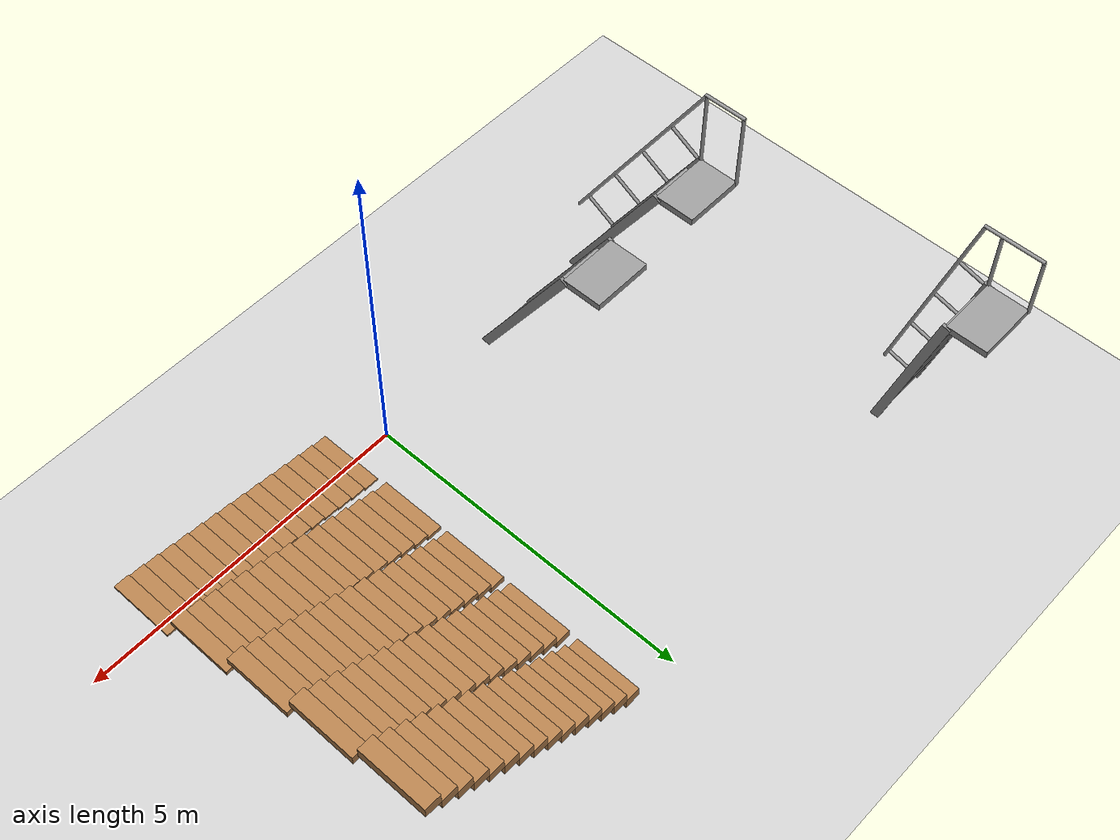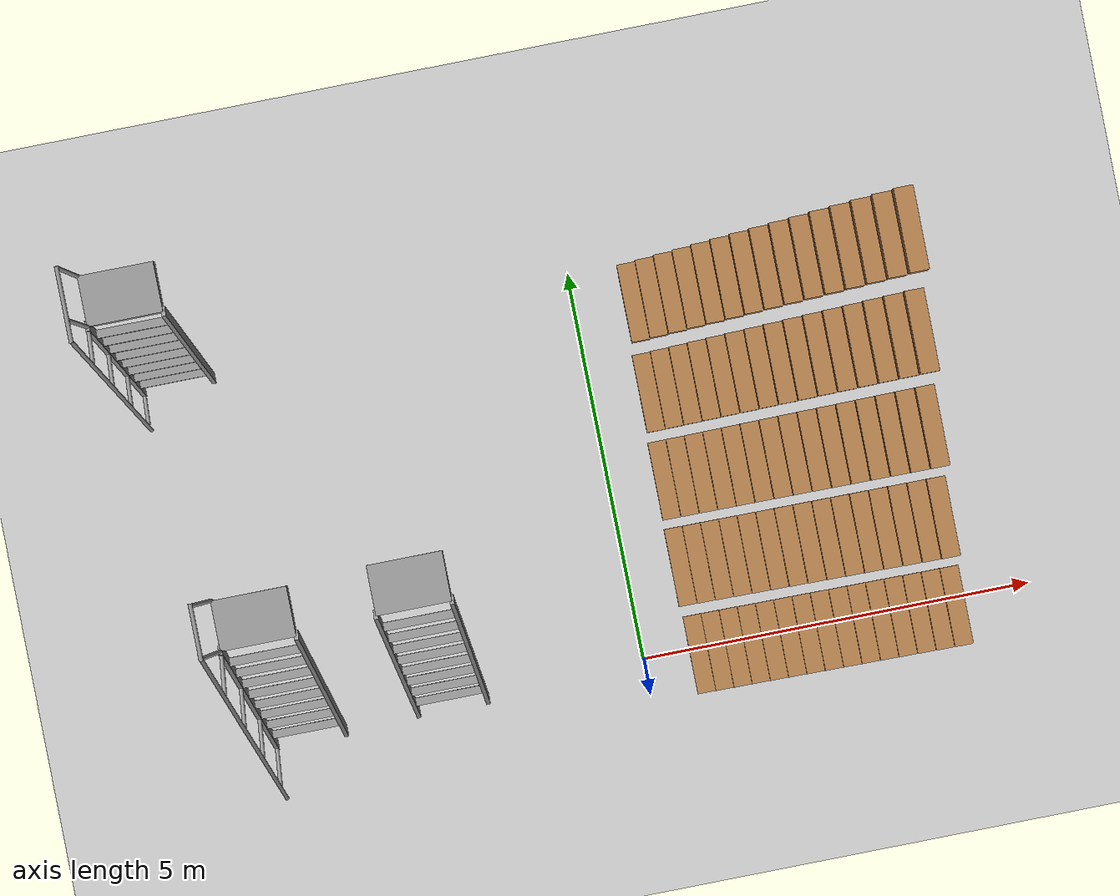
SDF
<sdf version="1.6">
 <world name="default">
  <light name="sun" type="directional">
   <pose>0 0 10 0 -0 0</pose>
   <diffuse>0.8 0.8 0.8 1</diffuse>
   <specular>0.2 0.2 0.2 1</specular>
   <attenuation>
    <range>1000</range>
    <constant>0.9</constant>
    <linear>0.01</linear>
    <quadratic>0.001</quadratic>
   </attenuation>
   <direction>-0.5 0.1 -0.9</direction>
  </light>
  <model name="ground_plane">
   <static>1</static>
   <link name="link">
    <collision name="collision">
     <geometry><plane><normal>0 0 1</normal><size>100 100</size></plane></geometry>
     <surface>
      <contact><collide_bitmask>65535</collide_bitmask></contact>
      <friction><ode><mu>100</mu><mu2>50</mu2></ode></friction>
     </surface>
    </collision>
    <visual name="visual">
     <cast_shadows>0</cast_shadows>
     <geometry><plane><normal>0 0 1</normal><size>100 100</size></plane></geometry>
     <material>
      <script><uri>file://media/materials/scripts/gazebo.material</uri><name>Gazebo/Grey</name></script>
     </material>
    </visual>
   </link>
  </model>
  <gravity>0 0 -9.8</gravity>
  <magnetic_field>6e-06 2.3e-05 -4.2e-05</magnetic_field>
  <atmosphere type="adiabatic"/>
  <physics name="default_physics" default="0" type="ode">
   <max_step_size>0.001</max_step_size>
   <real_time_factor>1</real_time_factor>
   <real_time_update_rate>1000</real_time_update_rate>
  </physics>
  <scene><ambient>0.4 0.4 0.4 1</ambient><background>0.7 0.7 0.7 1</background><shadows>1</shadows></scene>
  <spherical_coordinates>
   <surface_model>EARTH_WGS84</surface_model>
   <latitude_deg>0</latitude_deg>
   <longitude_deg>0</longitude_deg>
   <elevation>0</elevation>
   <heading_deg>0</heading_deg>
  </spherical_coordinates>
  <model name="ladder60with75">
   <model name="ladder_60deg_0rails">
    <static>1</static>
    <link name="step0">
     <pose>0 0.15396 0.266667 0 -0 0</pose>
     <inertial>
      <mass>9.75482</mass>
      <inertia>
       <ixx>0.00957124</ixx>
       <iyy>0.65963</iyy>
       <izz>0.666842</izz>
       <ixy>0</ixy>
       <ixz>0</ixz>
       <iyz>0</iyz>
      </inertia>
     </inertial>
     <collision name="collision"><geometry><box><size>0.9 0.1016 0.0381</size></box></geometry></collision>
     <visual name="visual">
      <geometry><box><size>0.9 0.1016 0.0381</size></box></geometry>
      <material>
       <script><uri>file://media/materials/scripts/gazebo.material</uri><name>Gazebo/Grey</name></script>
      </material>
     </visual>
    </link>
    <link name="step1">
     <pose>0 0.30792 0.533333 0 -0 0</pose>
     <inertial>
      <mass>9.75482</mass>
      <inertia>
       <ixx>0.00957124</ixx>
       <iyy>0.65963</iyy>
       <izz>0.666842</izz>
       <ixy>0</ixy>
       <ixz>0</ixz>
       <iyz>0</iyz>
      </inertia>
     </inertial>
     <collision name="collision"><geometry><box><size>0.9 0.1016 0.0381</size></box></geometry></collision>
     <visual name="visual">
      <geometry><box><size>0.9 0.1016 0.0381</size></box></geometry>
      <material>
       <script><uri>file://media/materials/scripts/gazebo.material</uri><name>Gazebo/Grey</name></script>
      </material>
     </visual>
    </link>
    <link name="step2">
     <pose>0 0.46188 0.8 0 -0 0</pose>
     <inertial>
      <mass>9.75482</mass>
      <inertia>
       <ixx>0.00957124</ixx>
       <iyy>0.65963</iyy>
       <izz>0.666842</izz>
       <ixy>0</ixy>
       <ixz>0</ixz>
       <iyz>0</iyz>
      </inertia>
     </inertial>
     <collision name="collision"><geometry><box><size>0.9 0.1016 0.0381</size></box></geometry></collision>
     <visual name="visual">
      <geometry><box><size>0.9 0.1016 0.0381</size></box></geometry>
      <material>
       <script><uri>file://media/materials/scripts/gazebo.material</uri><name>Gazebo/Grey</name></script>
      </material>
     </visual>
    </link>
    <link name="step3">
     <pose>0 0.61584 1.06667 0 -0 0</pose>
     <inertial>
      <mass>9.75482</mass>
      <inertia>
       <ixx>0.00957124</ixx>
       <iyy>0.65963</iyy>
       <izz>0.666842</izz>
       <ixy>0</ixy>
       <ixz>0</ixz>
       <iyz>0</iyz>
      </inertia>
     </inertial>
     <collision name="collision"><geometry><box><size>0.9 0.1016 0.0381</size></box></geometry></collision>
     <visual name="visual">
      <geometry><box><size>0.9 0.1016 0.0381</size></box></geometry>
      <material>
       <script><uri>file://media/materials/scripts/gazebo.material</uri><name>Gazebo/Grey</name></script>
      </material>
     </visual>
    </link>
    <link name="step4">
     <pose>0 0.7698 1.33333 0 -0 0</pose>
     <inertial>
      <mass>9.75482</mass>
      <inertia>
       <ixx>0.00957124</ixx>
       <iyy>0.65963</iyy>
       <izz>0.666842</izz>
       <ixy>0</ixy>
       <ixz>0</ixz>
       <iyz>0</iyz>
      </inertia>
     </inertial>
     <collision name="collision"><geometry><box><size>0.9 0.1016 0.0381</size></box></geometry></collision>
     <visual name="visual">
      <geometry><box><size>0.9 0.1016 0.0381</size></box></geometry>
      <material>
       <script><uri>file://media/materials/scripts/gazebo.material</uri><name>Gazebo/Grey</name></script>
      </material>
     </visual>
    </link>
    <link name="step5">
     <pose>0 0.92376 1.6 0 -0 0</pose>
     <inertial>
      <mass>9.75482</mass>
      <inertia>
       <ixx>0.00957124</ixx>
       <iyy>0.65963</iyy>
       <izz>0.666842</izz>
       <ixy>0</ixy>
       <ixz>0</ixz>
       <iyz>0</iyz>
      </inertia>
     </inertial>
     <collision name="collision"><geometry><box><size>0.9 0.1016 0.0381</size></box></geometry></collision>
     <visual name="visual">
      <geometry><box><size>0.9 0.1016 0.0381</size></box></geometry>
      <material>
       <script><uri>file://media/materials/scripts/gazebo.material</uri><name>Gazebo/Grey</name></script>
      </material>
     </visual>
    </link>
    <link name="step6">
     <pose>0 1.07772 1.86667 0 -0 0</pose>
     <inertial>
      <mass>9.75482</mass>
      <inertia>
       <ixx>0.00957124</ixx>
       <iyy>0.65963</iyy>
       <izz>0.666842</izz>
       <ixy>0</ixy>
       <ixz>0</ixz>
       <iyz>0</iyz>
      </inertia>
     </inertial>
     <collision name="collision"><geometry><box><size>0.9 0.1016 0.0381</size></box></geometry></collision>
     <visual name="visual">
      <geometry><box><size>0.9 0.1016 0.0381</size></box></geometry>
      <material>
       <script><uri>file://media/materials/scripts/gazebo.material</uri><name>Gazebo/Grey</name></script>
      </material>
     </visual>
    </link>
    <link name="step7">
     <pose>0 1.23168 2.13333 0 -0 0</pose>
     <inertial>
      <mass>9.75482</mass>
      <inertia>
       <ixx>0.00957124</ixx>
       <iyy>0.65963</iyy>
       <izz>0.666842</izz>
       <ixy>0</ixy>
       <ixz>0</ixz>
       <iyz>0</iyz>
      </inertia>
     </inertial>
     <collision name="collision"><geometry><box><size>0.9 0.1016 0.0381</size></box></geometry></collision>
     <visual name="visual">
      <geometry><box><size>0.9 0.1016 0.0381</size></box></geometry>
      <material>
       <script><uri>file://media/materials/scripts/gazebo.material</uri><name>Gazebo/Grey</name></script>
      </material>
     </visual>
    </link>
    <link name="landing">
     <pose>0 1.68564 2.4 0 -0 0</pose>
     <inertial>
      <mass>57.6072</mass>
      <inertia><ixx>1.73518</ixx><iyy>3.89545</iyy><izz>5.6167</izz><ixy>0</ixy><ixz>0</ixz><iyz>0</iyz></inertia>
     </inertial>
     <collision name="collision"><geometry><box><size>0.9 0.6 0.1016</size></box></geometry></collision>
     <visual name="visual">
      <geometry><box><size>0.9 0.6 0.1016</size></box></geometry>
      <material>
       <script><uri>file://media/materials/scripts/gazebo.material</uri><name>Gazebo/Grey</name></script>
      </material>
     </visual>
    </link>
    <link name="left_side_wall">
     <pose>-0.45 0.69282 1.2 1.0472 -0 0</pose>
     <collision name="collision"><geometry><box><size>0.0508 2.85128 0.13</size></box></geometry></collision>
     <visual name="visual">
      <geometry><box><size>0.0508 2.85128 0.13</size></box></geometry>
      <material>
       <script><uri>file://media/materials/scripts/gazebo.material</uri><name>Gazebo/Grey</name></script>
      </material>
     </visual>
    </link>
    <link name="right_side_wall">
     <pose>0.45 0.69282 1.2 1.0472 -0 0</pose>
     <collision name="collision"><geometry><box><size>0.0508 2.85128 0.13</size></box></geometry></collision>
     <visual name="visual">
      <geometry><box><size>0.0508 2.85128 0.13</size></box></geometry>
      <material>
       <script><uri>file://media/materials/scripts/gazebo.material</uri><name>Gazebo/Grey</name></script>
      </material>
     </visual>
    </link>
    <pose>1.4975 -1.54576 0 0 -0 0</pose>
   </model>
   <model name="ladder_60deg_1rails">
    <static>1</static>
    <link name="step0">
     <pose>0 0.15396 0.266667 0 -0 0</pose>
     <inertial>
      <mass>9.75482</mass>
      <inertia>
       <ixx>0.00957124</ixx>
       <iyy>0.65963</iyy>
       <izz>0.666842</izz>
       <ixy>0</ixy>
       <ixz>0</ixz>
       <iyz>0</iyz>
      </inertia>
     </inertial>
     <collision name="collision"><geometry><box><size>0.9 0.1016 0.0381</size></box></geometry></collision>
     <visual name="visual">
      <geometry><box><size>0.9 0.1016 0.0381</size></box></geometry>
      <material>
       <script><uri>file://media/materials/scripts/gazebo.material</uri><name>Gazebo/Grey</name></script>
      </material>
     </visual>
    </link>
    <link name="step1">
     <pose>0 0.30792 0.533333 0 -0 0</pose>
     <inertial>
      <mass>9.75482</mass>
      <inertia>
       <ixx>0.00957124</ixx>
       <iyy>0.65963</iyy>
       <izz>0.666842</izz>
       <ixy>0</ixy>
       <ixz>0</ixz>
       <iyz>0</iyz>
      </inertia>
     </inertial>
     <collision name="collision"><geometry><box><size>0.9 0.1016 0.0381</size></box></geometry></collision>
     <visual name="visual">
      <geometry><box><size>0.9 0.1016 0.0381</size></box></geometry>
      <material>
       <script><uri>file://media/materials/scripts/gazebo.material</uri><name>Gazebo/Grey</name></script>
      </material>
     </visual>
    </link>
    <link name="step2">
     <pose>0 0.46188 0.8 0 -0 0</pose>
     <inertial>
      <mass>9.75482</mass>
      <inertia>
       <ixx>0.00957124</ixx>
       <iyy>0.65963</iyy>
       <izz>0.666842</izz>
       <ixy>0</ixy>
       <ixz>0</ixz>
       <iyz>0</iyz>
      </inertia>
     </inertial>
     <collision name="collision"><geometry><box><size>0.9 0.1016 0.0381</size></box></geometry></collision>
     <visual name="visual">
      <geometry><box><size>0.9 0.1016 0.0381</size></box></geometry>
      <material>
       <script><uri>file://media/materials/scripts/gazebo.material</uri><name>Gazebo/Grey</name></script>
      </material>
     </visual>
    </link>
    <link name="step3">
     <pose>0 0.61584 1.06667 0 -0 0</pose>
     <inertial>
      <mass>9.75482</mass>
      <inertia>
       <ixx>0.00957124</ixx>
       <iyy>0.65963</iyy>
       <izz>0.666842</izz>
       <ixy>0</ixy>
       <ixz>0</ixz>
       <iyz>0</iyz>
      </inertia>
     </inertial>
     <collision name="collision"><geometry><box><size>0.9 0.1016 0.0381</size></box></geometry></collision>
     <visual name="visual">
      <geometry><box><size>0.9 0.1016 0.0381</size></box></geometry>
      <material>
       <script><uri>file://media/materials/scripts/gazebo.material</uri><name>Gazebo/Grey</name></script>
      </material>
     </visual>
    </link>
    <link name="step4">
     <pose>0 0.7698 1.33333 0 -0 0</pose>
     <inertial>
      <mass>9.75482</mass>
      <inertia>
       <ixx>0.00957124</ixx>
       <iyy>0.65963</iyy>
       <izz>0.666842</izz>
       <ixy>0</ixy>
       <ixz>0</ixz>
       <iyz>0</iyz>
      </inertia>
     </inertial>
     <collision name="collision"><geometry><box><size>0.9 0.1016 0.0381</size></box></geometry></collision>
     <visual name="visual">
      <geometry><box><size>0.9 0.1016 0.0381</size></box></geometry>
      <material>
       <script><uri>file://media/materials/scripts/gazebo.material</uri><name>Gazebo/Grey</name></script>
      </material>
     </visual>
    </link>
    <link name="step5">
     <pose>0 0.92376 1.6 0 -0 0</pose>
     <inertial>
      <mass>9.75482</mass>
      <inertia>
       <ixx>0.00957124</ixx>
       <iyy>0.65963</iyy>
       <izz>0.666842</izz>
       <ixy>0</ixy>
       <ixz>0</ixz>
       <iyz>0</iyz>
      </inertia>
     </inertial>
     <collision name="collision"><geometry><box><size>0.9 0.1016 0.0381</size></box></geometry></collision>
     <visual name="visual">
      <geometry><box><size>0.9 0.1016 0.0381</size></box></geometry>
      <material>
       <script><uri>file://media/materials/scripts/gazebo.material</uri><name>Gazebo/Grey</name></script>
      </material>
     </visual>
    </link>
    <link name="step6">
     <pose>0 1.07772 1.86667 0 -0 0</pose>
     <inertial>
      <mass>9.75482</mass>
      <inertia>
       <ixx>0.00957124</ixx>
       <iyy>0.65963</iyy>
       <izz>0.666842</izz>
       <ixy>0</ixy>
       <ixz>0</ixz>
       <iyz>0</iyz>
      </inertia>
     </inertial>
     <collision name="collision"><geometry><box><size>0.9 0.1016 0.0381</size></box></geometry></collision>
     <visual name="visual">
      <geometry><box><size>0.9 0.1016 0.0381</size></box></geometry>
      <material>
       <script><uri>file://media/materials/scripts/gazebo.material</uri><name>Gazebo/Grey</name></script>
      </material>
     </visual>
    </link>
    <link name="step7">
     <pose>0 1.23168 2.13333 0 -0 0</pose>
     <inertial>
      <mass>9.75482</mass>
      <inertia>
       <ixx>0.00957124</ixx>
       <iyy>0.65963</iyy>
       <izz>0.666842</izz>
       <ixy>0</ixy>
       <ixz>0</ixz>
       <iyz>0</iyz>
      </inertia>
     </inertial>
     <collision name="collision"><geometry><box><size>0.9 0.1016 0.0381</size></box></geometry></collision>
     <visual name="visual">
      <geometry><box><size>0.9 0.1016 0.0381</size></box></geometry>
      <material>
       <script><uri>file://media/materials/scripts/gazebo.material</uri><name>Gazebo/Grey</name></script>
      </material>
     </visual>
    </link>
    <link name="landing">
     <pose>0 1.68564 2.4 0 -0 0</pose>
     <inertial>
      <mass>57.6072</mass>
      <inertia><ixx>1.73518</ixx><iyy>3.89545</iyy><izz>5.6167</izz><ixy>0</ixy><ixz>0</ixz><iyz>0</iyz></inertia>
     </inertial>
     <collision name="collision"><geometry><box><size>0.9 0.6 0.1016</size></box></geometry></collision>
     <visual name="visual">
      <geometry><box><size>0.9 0.6 0.1016</size></box></geometry>
      <material>
       <script><uri>file://media/materials/scripts/gazebo.material</uri><name>Gazebo/Grey</name></script>
      </material>
     </visual>
    </link>
    <link name="left_side_wall">
     <pose>-0.45 0.69282 1.2 1.0472 -0 0</pose>
     <collision name="collision"><geometry><box><size>0.0508 2.85128 0.13</size></box></geometry></collision>
     <visual name="visual">
      <geometry><box><size>0.0508 2.85128 0.13</size></box></geometry>
      <material>
       <script><uri>file://media/materials/scripts/gazebo.material</uri><name>Gazebo/Grey</name></script>
      </material>
     </visual>
    </link>
    <link name="right_side_wall">
     <pose>0.45 0.69282 1.2 1.0472 -0 0</pose>
     <collision name="collision"><geometry><box><size>0.0508 2.85128 0.13</size></box></geometry></collision>
     <visual name="visual">
      <geometry><box><size>0.0508 2.85128 0.13</size></box></geometry>
      <material>
       <script><uri>file://media/materials/scripts/gazebo.material</uri><name>Gazebo/Grey</name></script>
      </material>
     </visual>
    </link>
    <link name="left_railing_long">
     <pose>-0.45 0.34282 1.80622 -0.523599 0 0</pose>
     <collision name="collision">
      <geometry><cylinder><radius>0.02413</radius><length>4.17128</length></cylinder></geometry>
     </collision>
     <visual name="visual">
      <geometry><cylinder><radius>0.02413</radius><length>4.17128</length></cylinder></geometry>
      <material>
       <script><uri>file://media/materials/scripts/gazebo.material</uri><name>Gazebo/Grey</name></script>
      </material>
     </visual>
    </link>
    <link name="left_railing_upright0">
     <pose>-0.45 -0.274963 0.15875 1.0472 -0 0</pose>
     <collision name="collision">
      <geometry><cylinder><radius>0.02413</radius><length>0.541218</length></cylinder></geometry>
     </collision>
     <visual name="visual">
      <geometry><cylinder><radius>0.02413</radius><length>0.541218</length></cylinder></geometry>
      <material>
       <script><uri>file://media/materials/scripts/gazebo.material</uri><name>Gazebo/Grey</name></script>
      </material>
     </visual>
    </link>
    <link name="left_railing_upright1">
     <pose>-0.45 0.186917 0.95875 1.0472 -0 0</pose>
     <collision name="collision">
      <geometry><cylinder><radius>0.02413</radius><length>0.541218</length></cylinder></geometry>
     </collision>
     <visual name="visual">
      <geometry><cylinder><radius>0.02413</radius><length>0.541218</length></cylinder></geometry>
      <material>
       <script><uri>file://media/materials/scripts/gazebo.material</uri><name>Gazebo/Grey</name></script>
      </material>
     </visual>
    </link>
    <link name="left_railing_upright2">
     <pose>-0.45 0.648797 1.75875 1.0472 -0 0</pose>
     <collision name="collision">
      <geometry><cylinder><radius>0.02413</radius><length>0.541218</length></cylinder></geometry>
     </collision>
     <visual name="visual">
      <geometry><cylinder><radius>0.02413</radius><length>0.541218</length></cylinder></geometry>
      <material>
       <script><uri>file://media/materials/scripts/gazebo.material</uri><name>Gazebo/Grey</name></script>
      </material>
     </visual>
    </link>
    <link name="left_railing_upright3">
     <pose>-0.45 1.11068 2.55875 1.0472 -0 0</pose>
     <collision name="collision">
      <geometry><cylinder><radius>0.02413</radius><length>0.541218</length></cylinder></geometry>
     </collision>
     <visual name="visual">
      <geometry><cylinder><radius>0.02413</radius><length>0.541218</length></cylinder></geometry>
      <material>
       <script><uri>file://media/materials/scripts/gazebo.material</uri><name>Gazebo/Grey</name></script>
      </material>
     </visual>
    </link>
    <link name="left_railing_landing_top">
     <pose>-0.45 1.68564 3.61244 1.5708 -0 0</pose>
     <collision name="collision">
      <geometry><cylinder><radius>0.02413</radius><length>0.64826</length></cylinder></geometry>
     </collision>
     <visual name="visual">
      <geometry><cylinder><radius>0.02413</radius><length>0.64826</length></cylinder></geometry>
      <material>
       <script><uri>file://media/materials/scripts/gazebo.material</uri><name>Gazebo/Grey</name></script>
      </material>
     </visual>
    </link>
    <link name="left_railing_landing_upright_0">
     <pose>-0.45 1.38564 3.00622 0 -0 0</pose>
     <collision name="collision">
      <geometry><cylinder><radius>0.02413</radius><length>1.21244</length></cylinder></geometry>
     </collision>
     <visual name="visual">
      <geometry><cylinder><radius>0.02413</radius><length>1.21244</length></cylinder></geometry>
      <material>
       <script><uri>file://media/materials/scripts/gazebo.material</uri><name>Gazebo/Grey</name></script>
      </material>
     </visual>
    </link>
    <link name="left_railing_landing_upright_1">
     <pose>-0.45 1.98564 3.00622 0 -0 0</pose>
     <collision name="collision">
      <geometry><cylinder><radius>0.02413</radius><length>1.21244</length></cylinder></geometry>
     </collision>
     <visual name="visual">
      <geometry><cylinder><radius>0.02413</radius><length>1.21244</length></cylinder></geometry>
      <material>
       <script><uri>file://media/materials/scripts/gazebo.material</uri><name>Gazebo/Grey</name></script>
      </material>
     </visual>
    </link>
    <pose>-0.355505 -1.59937 0 0 -0 0</pose>
   </model>
   <model name="ladder_75deg_1rails">
    <static>1</static>
    <link name="step0">
     <pose>0 0.071453 0.266667 0 -0 0</pose>
     <inertial>
      <mass>9.75482</mass>
      <inertia>
       <ixx>0.00957124</ixx>
       <iyy>0.65963</iyy>
       <izz>0.666842</izz>
       <ixy>0</ixy>
       <ixz>0</ixz>
       <iyz>0</iyz>
      </inertia>
     </inertial>
     <collision name="collision"><geometry><box><size>0.9 0.1016 0.0381</size></box></geometry></collision>
     <visual name="visual">
      <geometry><box><size>0.9 0.1016 0.0381</size></box></geometry>
      <material>
       <script><uri>file://media/materials/scripts/gazebo.material</uri><name>Gazebo/Grey</name></script>
      </material>
     </visual>
    </link>
    <link name="step1">
     <pose>0 0.142906 0.533333 0 -0 0</pose>
     <inertial>
      <mass>9.75482</mass>
      <inertia>
       <ixx>0.00957124</ixx>
       <iyy>0.65963</iyy>
       <izz>0.666842</izz>
       <ixy>0</ixy>
       <ixz>0</ixz>
       <iyz>0</iyz>
      </inertia>
     </inertial>
     <collision name="collision"><geometry><box><size>0.9 0.1016 0.0381</size></box></geometry></collision>
     <visual name="visual">
      <geometry><box><size>0.9 0.1016 0.0381</size></box></geometry>
      <material>
       <script><uri>file://media/materials/scripts/gazebo.material</uri><name>Gazebo/Grey</name></script>
      </material>
     </visual>
    </link>
    <link name="step2">
     <pose>0 0.214359 0.8 0 -0 0</pose>
     <inertial>
      <mass>9.75482</mass>
      <inertia>
       <ixx>0.00957124</ixx>
       <iyy>0.65963</iyy>
       <izz>0.666842</izz>
       <ixy>0</ixy>
       <ixz>0</ixz>
       <iyz>0</iyz>
      </inertia>
     </inertial>
     <collision name="collision"><geometry><box><size>0.9 0.1016 0.0381</size></box></geometry></collision>
     <visual name="visual">
      <geometry><box><size>0.9 0.1016 0.0381</size></box></geometry>
      <material>
       <script><uri>file://media/materials/scripts/gazebo.material</uri><name>Gazebo/Grey</name></script>
      </material>
     </visual>
    </link>
    <link name="step3">
     <pose>0 0.285812 1.06667 0 -0 0</pose>
     <inertial>
      <mass>9.75482</mass>
      <inertia>
       <ixx>0.00957124</ixx>
       <iyy>0.65963</iyy>
       <izz>0.666842</izz>
       <ixy>0</ixy>
       <ixz>0</ixz>
       <iyz>0</iyz>
      </inertia>
     </inertial>
     <collision name="collision"><geometry><box><size>0.9 0.1016 0.0381</size></box></geometry></collision>
     <visual name="visual">
      <geometry><box><size>0.9 0.1016 0.0381</size></box></geometry>
      <material>
       <script><uri>file://media/materials/scripts/gazebo.material</uri><name>Gazebo/Grey</name></script>
      </material>
     </visual>
    </link>
    <link name="step4">
     <pose>0 0.357266 1.33333 0 -0 0</pose>
     <inertial>
      <mass>9.75482</mass>
      <inertia>
       <ixx>0.00957124</ixx>
       <iyy>0.65963</iyy>
       <izz>0.666842</izz>
       <ixy>0</ixy>
       <ixz>0</ixz>
       <iyz>0</iyz>
      </inertia>
     </inertial>
     <collision name="collision"><geometry><box><size>0.9 0.1016 0.0381</size></box></geometry></collision>
     <visual name="visual">
      <geometry><box><size>0.9 0.1016 0.0381</size></box></geometry>
      <material>
       <script><uri>file://media/materials/scripts/gazebo.material</uri><name>Gazebo/Grey</name></script>
      </material>
     </visual>
    </link>
    <link name="step5">
     <pose>0 0.428719 1.6 0 -0 0</pose>
     <inertial>
      <mass>9.75482</mass>
      <inertia>
       <ixx>0.00957124</ixx>
       <iyy>0.65963</iyy>
       <izz>0.666842</izz>
       <ixy>0</ixy>
       <ixz>0</ixz>
       <iyz>0</iyz>
      </inertia>
     </inertial>
     <collision name="collision"><geometry><box><size>0.9 0.1016 0.0381</size></box></geometry></collision>
     <visual name="visual">
      <geometry><box><size>0.9 0.1016 0.0381</size></box></geometry>
      <material>
       <script><uri>file://media/materials/scripts/gazebo.material</uri><name>Gazebo/Grey</name></script>
      </material>
     </visual>
    </link>
    <link name="step6">
     <pose>0 0.500172 1.86667 0 -0 0</pose>
     <inertial>
      <mass>9.75482</mass>
      <inertia>
       <ixx>0.00957124</ixx>
       <iyy>0.65963</iyy>
       <izz>0.666842</izz>
       <ixy>0</ixy>
       <ixz>0</ixz>
       <iyz>0</iyz>
      </inertia>
     </inertial>
     <collision name="collision"><geometry><box><size>0.9 0.1016 0.0381</size></box></geometry></collision>
     <visual name="visual">
      <geometry><box><size>0.9 0.1016 0.0381</size></box></geometry>
      <material>
       <script><uri>file://media/materials/scripts/gazebo.material</uri><name>Gazebo/Grey</name></script>
      </material>
     </visual>
    </link>
    <link name="step7">
     <pose>0 0.571625 2.13333 0 -0 0</pose>
     <inertial>
      <mass>9.75482</mass>
      <inertia>
       <ixx>0.00957124</ixx>
       <iyy>0.65963</iyy>
       <izz>0.666842</izz>
       <ixy>0</ixy>
       <ixz>0</ixz>
       <iyz>0</iyz>
      </inertia>
     </inertial>
     <collision name="collision"><geometry><box><size>0.9 0.1016 0.0381</size></box></geometry></collision>
     <visual name="visual">
      <geometry><box><size>0.9 0.1016 0.0381</size></box></geometry>
      <material>
       <script><uri>file://media/materials/scripts/gazebo.material</uri><name>Gazebo/Grey</name></script>
      </material>
     </visual>
    </link>
    <link name="landing">
     <pose>0 0.943078 2.4 0 -0 0</pose>
     <inertial>
      <mass>57.6072</mass>
      <inertia><ixx>1.73518</ixx><iyy>3.89545</iyy><izz>5.6167</izz><ixy>0</ixy><ixz>0</ixz><iyz>0</iyz></inertia>
     </inertial>
     <collision name="collision"><geometry><box><size>0.9 0.6 0.1016</size></box></geometry></collision>
     <visual name="visual">
      <geometry><box><size>0.9 0.6 0.1016</size></box></geometry>
      <material>
       <script><uri>file://media/materials/scripts/gazebo.material</uri><name>Gazebo/Grey</name></script>
      </material>
     </visual>
    </link>
    <link name="left_side_wall">
     <pose>-0.45 0.321539 1.2 1.309 -0 0</pose>
     <collision name="collision"><geometry><box><size>0.0508 2.56466 0.13</size></box></geometry></collision>
     <visual name="visual">
      <geometry><box><size>0.0508 2.56466 0.13</size></box></geometry>
      <material>
       <script><uri>file://media/materials/scripts/gazebo.material</uri><name>Gazebo/Grey</name></script>
      </material>
     </visual>
    </link>
    <link name="right_side_wall">
     <pose>0.45 0.321539 1.2 1.309 -0 0</pose>
     <collision name="collision"><geometry><box><size>0.0508 2.56466 0.13</size></box></geometry></collision>
     <visual name="visual">
      <geometry><box><size>0.0508 2.56466 0.13</size></box></geometry>
      <material>
       <script><uri>file://media/materials/scripts/gazebo.material</uri><name>Gazebo/Grey</name></script>
      </material>
     </visual>
    </link>
    <link name="left_railing_long">
     <pose>-0.45 -0.053461 1.66651 -0.261799 0 0</pose>
     <collision name="collision">
      <geometry><cylinder><radius>0.02413</radius><length>3.51529</length></cylinder></geometry>
     </collision>
     <visual name="visual">
      <geometry><cylinder><radius>0.02413</radius><length>3.51529</length></cylinder></geometry>
      <material>
       <script><uri>file://media/materials/scripts/gazebo.material</uri><name>Gazebo/Grey</name></script>
      </material>
     </visual>
    </link>
    <link name="left_railing_upright0">
     <pose>-0.45 -0.210089 0.056293 1.309 -0 0</pose>
     <collision name="collision">
      <geometry><cylinder><radius>0.02413</radius><length>0.482963</length></cylinder></geometry>
     </collision>
     <visual name="visual">
      <geometry><cylinder><radius>0.02413</radius><length>0.482963</length></cylinder></geometry>
      <material>
       <script><uri>file://media/materials/scripts/gazebo.material</uri><name>Gazebo/Grey</name></script>
      </material>
     </visual>
    </link>
    <link name="left_railing_upright1">
     <pose>-0.45 0.00427 0.856293 1.309 -0 0</pose>
     <collision name="collision">
      <geometry><cylinder><radius>0.02413</radius><length>0.482963</length></cylinder></geometry>
     </collision>
     <visual name="visual">
      <geometry><cylinder><radius>0.02413</radius><length>0.482963</length></cylinder></geometry>
      <material>
       <script><uri>file://media/materials/scripts/gazebo.material</uri><name>Gazebo/Grey</name></script>
      </material>
     </visual>
    </link>
    <link name="left_railing_upright2">
     <pose>-0.45 0.21863 1.65629 1.309 -0 0</pose>
     <collision name="collision">
      <geometry><cylinder><radius>0.02413</radius><length>0.482963</length></cylinder></geometry>
     </collision>
     <visual name="visual">
      <geometry><cylinder><radius>0.02413</radius><length>0.482963</length></cylinder></geometry>
      <material>
       <script><uri>file://media/materials/scripts/gazebo.material</uri><name>Gazebo/Grey</name></script>
      </material>
     </visual>
    </link>
    <link name="left_railing_upright3">
     <pose>-0.45 0.432989 2.45629 1.309 -0 0</pose>
     <collision name="collision">
      <geometry><cylinder><radius>0.02413</radius><length>0.482963</length></cylinder></geometry>
     </collision>
     <visual name="visual">
      <geometry><cylinder><radius>0.02413</radius><length>0.482963</length></cylinder></geometry>
      <material>
       <script><uri>file://media/materials/scripts/gazebo.material</uri><name>Gazebo/Grey</name></script>
      </material>
     </visual>
    </link>
    <link name="left_railing_landing_top">
     <pose>-0.45 0.818078 3.35714 1.5708 -0 0</pose>
     <collision name="collision">
      <geometry><cylinder><radius>0.02413</radius><length>0.87413</length></cylinder></geometry>
     </collision>
     <visual name="visual">
      <geometry><cylinder><radius>0.02413</radius><length>0.87413</length></cylinder></geometry>
      <material>
       <script><uri>file://media/materials/scripts/gazebo.material</uri><name>Gazebo/Grey</name></script>
      </material>
     </visual>
    </link>
    <link name="left_railing_landing_upright_0">
     <pose>-0.45 0.643078 2.86651 0 -0 0</pose>
     <collision name="collision">
      <geometry><cylinder><radius>0.02413</radius><length>0.933013</length></cylinder></geometry>
     </collision>
     <visual name="visual">
      <geometry><cylinder><radius>0.02413</radius><length>0.933013</length></cylinder></geometry>
      <material>
       <script><uri>file://media/materials/scripts/gazebo.material</uri><name>Gazebo/Grey</name></script>
      </material>
     </visual>
    </link>
    <link name="left_railing_landing_upright_1">
     <pose>-0.45 1.24308 2.86651 0 -0 0</pose>
     <collision name="collision">
      <geometry><cylinder><radius>0.02413</radius><length>0.933013</length></cylinder></geometry>
     </collision>
     <visual name="visual">
      <geometry><cylinder><radius>0.02413</radius><length>0.933013</length></cylinder></geometry>
      <material>
       <script><uri>file://media/materials/scripts/gazebo.material</uri><name>Gazebo/Grey</name></script>
      </material>
     </visual>
    </link>
    <pose>-1.14199 3.14513 0 0 -0 0</pose>
   </model>
   <static>0</static>
   <pose>-4.00317 1.4328 0 0 -0 0</pose>
  </model>
  <model name="stairs_4group">
   <pose>2.34848 2.20062 0 0 -0 0</pose>
   <link name="Stairs_0">
    <visual name="Stairs_0_Visual_0">
     <pose>-1.66333 -1.135 0.033333 0 -0 1.5708</pose>
     <geometry><box><size>1 0.233333 0.066667</size></box></geometry>
     <material>
      <script><uri>file://media/materials/scripts/gazebo.material</uri><name>Gazebo/Wood</name></script>
      <ambient>0.996078 0.47451 0.0196078 1</ambient>
     </material>
     <meta><layer>0</layer></meta>
    </visual>
    <collision name="Stairs_0_Collision_0">
     <geometry><box><size>1 0.233333 0.066667</size></box></geometry>
     <pose>-1.66333 -1.135 0.033333 0 -0 1.5708</pose>
    </collision>
    <visual name="Stairs_0_Visual_1">
     <pose>-1.43 -1.135 0.1 0 -0 1.5708</pose>
     <geometry><box><size>1 0.233333 0.066667</size></box></geometry>
     <material>
      <script><uri>file://media/materials/scripts/gazebo.material</uri><name>Gazebo/Wood</name></script>
      <ambient>0.996078 0.47451 0.0196078 1</ambient>
     </material>
     <meta><layer>0</layer></meta>
    </visual>
    <collision name="Stairs_0_Collision_1">
     <geometry><box><size>1 0.233333 0.066667</size></box></geometry>
     <pose>-1.43 -1.135 0.1 0 -0 1.5708</pose>
    </collision>
    <visual name="Stairs_0_Visual_2">
     <pose>-1.19667 -1.135 0.166667 0 -0 1.5708</pose>
     <geometry><box><size>1 0.233333 0.066667</size></box></geometry>
     <material>
      <script><uri>file://media/materials/scripts/gazebo.material</uri><name>Gazebo/Wood</name></script>
      <ambient>0.996078 0.47451 0.0196078 1</ambient>
     </material>
     <meta><layer>0</layer></meta>
    </visual>
    <collision name="Stairs_0_Collision_2">
     <geometry><box><size>1 0.233333 0.066667</size></box></geometry>
     <pose>-1.19667 -1.135 0.166667 0 -0 1.5708</pose>
    </collision>
    <visual name="Stairs_0_Visual_3">
     <pose>-0.963333 -1.135 0.233333 0 -0 1.5708</pose>
     <geometry><box><size>1 0.233333 0.066667</size></box></geometry>
     <material>
      <script><uri>file://media/materials/scripts/gazebo.material</uri><name>Gazebo/Wood</name></script>
      <ambient>0.996078 0.47451 0.0196078 1</ambient>
     </material>
     <meta><layer>0</layer></meta>
    </visual>
    <collision name="Stairs_0_Collision_3">
     <geometry><box><size>1 0.233333 0.066667</size></box></geometry>
     <pose>-0.963333 -1.135 0.233333 0 -0 1.5708</pose>
    </collision>
    <visual name="Stairs_0_Visual_4">
     <pose>-0.73 -1.135 0.3 0 -0 1.5708</pose>
     <geometry><box><size>1 0.233333 0.066667</size></box></geometry>
     <material>
      <script><uri>file://media/materials/scripts/gazebo.material</uri><name>Gazebo/Wood</name></script>
      <ambient>0.996078 0.47451 0.0196078 1</ambient>
     </material>
     <meta><layer>0</layer></meta>
    </visual>
    <collision name="Stairs_0_Collision_4">
     <geometry><box><size>1 0.233333 0.066667</size></box></geometry>
     <pose>-0.73 -1.135 0.3 0 -0 1.5708</pose>
    </collision>
    <visual name="Stairs_0_Visual_5">
     <pose>-0.496667 -1.135 0.366667 0 -0 1.5708</pose>
     <geometry><box><size>1 0.233333 0.066667</size></box></geometry>
     <material>
      <script><uri>file://media/materials/scripts/gazebo.material</uri><name>Gazebo/Wood</name></script>
      <ambient>0.996078 0.47451 0.0196078 1</ambient>
     </material>
     <meta><layer>0</layer></meta>
    </visual>
    <collision name="Stairs_0_Collision_5">
     <geometry><box><size>1 0.233333 0.066667</size></box></geometry>
     <pose>-0.496667 -1.135 0.366667 0 -0 1.5708</pose>
    </collision>
    <visual name="Stairs_0_Visual_6">
     <pose>-0.263333 -1.135 0.433333 0 -0 1.5708</pose>
     <geometry><box><size>1 0.233333 0.066667</size></box></geometry>
     <material>
      <script><uri>file://media/materials/scripts/gazebo.material</uri><name>Gazebo/Wood</name></script>
      <ambient>0.996078 0.47451 0.0196078 1</ambient>
     </material>
     <meta><layer>0</layer></meta>
    </visual>
    <collision name="Stairs_0_Collision_6">
     <geometry><box><size>1 0.233333 0.066667</size></box></geometry>
     <pose>-0.263333 -1.135 0.433333 0 -0 1.5708</pose>
    </collision>
    <visual name="Stairs_0_Visual_7">
     <pose>-0.03 -1.135 0.5 0 -0 1.5708</pose>
     <geometry><box><size>1 0.233333 0.066667</size></box></geometry>
     <material>
      <script><uri>file://media/materials/scripts/gazebo.material</uri><name>Gazebo/Wood</name></script>
      <ambient>0.996078 0.47451 0.0196078 1</ambient>
     </material>
     <meta><layer>0</layer></meta>
    </visual>
    <collision name="Stairs_0_Collision_7">
     <geometry><box><size>1 0.233333 0.066667</size></box></geometry>
     <pose>-0.03 -1.135 0.5 0 -0 1.5708</pose>
    </collision>
    <visual name="Stairs_0_Visual_8">
     <pose>0.203334 -1.135 0.566667 0 -0 1.5708</pose>
     <geometry><box><size>1 0.233333 0.066667</size></box></geometry>
     <material>
      <script><uri>file://media/materials/scripts/gazebo.material</uri><name>Gazebo/Wood</name></script>
      <ambient>0.996078 0.47451 0.0196078 1</ambient>
     </material>
     <meta><layer>0</layer></meta>
    </visual>
    <collision name="Stairs_0_Collision_8">
     <geometry><box><size>1 0.233333 0.066667</size></box></geometry>
     <pose>0.203334 -1.135 0.566667 0 -0 1.5708</pose>
    </collision>
    <visual name="Stairs_0_Visual_9">
     <pose>0.436667 -1.135 0.633333 0 -0 1.5708</pose>
     <geometry><box><size>1 0.233333 0.066667</size></box></geometry>
     <material>
      <script><uri>file://media/materials/scripts/gazebo.material</uri><name>Gazebo/Wood</name></script>
      <ambient>0.996078 0.47451 0.0196078 1</ambient>
     </material>
     <meta><layer>0</layer></meta>
    </visual>
    <collision name="Stairs_0_Collision_9">
     <geometry><box><size>1 0.233333 0.066667</size></box></geometry>
     <pose>0.436667 -1.135 0.633333 0 -0 1.5708</pose>
    </collision>
    <visual name="Stairs_0_Visual_10">
     <pose>0.67 -1.135 0.7 0 -0 1.5708</pose>
     <geometry><box><size>1 0.233333 0.066667</size></box></geometry>
     <material>
      <script><uri>file://media/materials/scripts/gazebo.material</uri><name>Gazebo/Wood</name></script>
      <ambient>0.996078 0.47451 0.0196078 1</ambient>
     </material>
     <meta><layer>0</layer></meta>
    </visual>
    <collision name="Stairs_0_Collision_10">
     <geometry><box><size>1 0.233333 0.066667</size></box></geometry>
     <pose>0.67 -1.135 0.7 0 -0 1.5708</pose>
    </collision>
    <visual name="Stairs_0_Visual_11">
     <pose>0.903333 -1.135 0.766667 0 -0 1.5708</pose>
     <geometry><box><size>1 0.233333 0.066667</size></box></geometry>
     <material>
      <script><uri>file://media/materials/scripts/gazebo.material</uri><name>Gazebo/Wood</name></script>
      <ambient>0.996078 0.47451 0.0196078 1</ambient>
     </material>
     <meta><layer>0</layer></meta>
    </visual>
    <collision name="Stairs_0_Collision_11">
     <geometry><box><size>1 0.233333 0.066667</size></box></geometry>
     <pose>0.903333 -1.135 0.766667 0 -0 1.5708</pose>
    </collision>
    <visual name="Stairs_0_Visual_12">
     <pose>1.13667 -1.135 0.833333 0 -0 1.5708</pose>
     <geometry><box><size>1 0.233333 0.066667</size></box></geometry>
     <material>
      <script><uri>file://media/materials/scripts/gazebo.material</uri><name>Gazebo/Wood</name></script>
      <ambient>0.996078 0.47451 0.0196078 1</ambient>
     </material>
     <meta><layer>0</layer></meta>
    </visual>
    <collision name="Stairs_0_Collision_12">
     <geometry><box><size>1 0.233333 0.066667</size></box></geometry>
     <pose>1.13667 -1.135 0.833333 0 -0 1.5708</pose>
    </collision>
    <visual name="Stairs_0_Visual_13">
     <pose>1.37 -1.135 0.9 0 -0 1.5708</pose>
     <geometry><box><size>1 0.233333 0.066667</size></box></geometry>
     <material>
      <script><uri>file://media/materials/scripts/gazebo.material</uri><name>Gazebo/Wood</name></script>
      <ambient>0.996078 0.47451 0.0196078 1</ambient>
     </material>
     <meta><layer>0</layer></meta>
    </visual>
    <collision name="Stairs_0_Collision_13">
     <geometry><box><size>1 0.233333 0.066667</size></box></geometry>
     <pose>1.37 -1.135 0.9 0 -0 1.5708</pose>
    </collision>
    <visual name="Stairs_0_Visual_14">
     <pose>1.60333 -1.135 0.966667 0 -0 1.5708</pose>
     <geometry><box><size>1 0.233333 0.066667</size></box></geometry>
     <material>
      <script><uri>file://media/materials/scripts/gazebo.material</uri><name>Gazebo/Wood</name></script>
      <ambient>0.996078 0.47451 0.0196078 1</ambient>
     </material>
     <meta><layer>0</layer></meta>
    </visual>
    <collision name="Stairs_0_Collision_14">
     <geometry><box><size>1 0.233333 0.066667</size></box></geometry>
     <pose>1.60333 -1.135 0.966667 0 -0 1.5708</pose>
    </collision>
   </link>
   <link name="Stairs_2">
    <visual name="Stairs_2_Visual_0">
     <pose>-1.64333 -2.275 0.016667 0 -0 1.5708</pose>
     <geometry><box><size>1 0.233333 0.033333</size></box></geometry>
     <material>
      <script><uri>file://media/materials/scripts/gazebo.material</uri><name>Gazebo/Wood</name></script>
      <ambient>1 1 1 1</ambient>
     </material>
     <meta><layer>0</layer></meta>
    </visual>
    <collision name="Stairs_2_Collision_0">
     <geometry><box><size>1 0.233333 0.033333</size></box></geometry>
     <pose>-1.64333 -2.275 0.016667 0 -0 1.5708</pose>
    </collision>
    <visual name="Stairs_2_Visual_1">
     <pose>-1.41 -2.275 0.05 0 -0 1.5708</pose>
     <geometry><box><size>1 0.233333 0.033333</size></box></geometry>
     <material>
      <script><uri>file://media/materials/scripts/gazebo.material</uri><name>Gazebo/Wood</name></script>
      <ambient>1 1 1 1</ambient>
     </material>
     <meta><layer>0</layer></meta>
    </visual>
    <collision name="Stairs_2_Collision_1">
     <geometry><box><size>1 0.233333 0.033333</size></box></geometry>
     <pose>-1.41 -2.275 0.05 0 -0 1.5708</pose>
    </collision>
    <visual name="Stairs_2_Visual_2">
     <pose>-1.17667 -2.275 0.083333 0 -0 1.5708</pose>
     <geometry><box><size>1 0.233333 0.033333</size></box></geometry>
     <material>
      <script><uri>file://media/materials/scripts/gazebo.material</uri><name>Gazebo/Wood</name></script>
      <ambient>1 1 1 1</ambient>
     </material>
     <meta><layer>0</layer></meta>
    </visual>
    <collision name="Stairs_2_Collision_2">
     <geometry><box><size>1 0.233333 0.033333</size></box></geometry>
     <pose>-1.17667 -2.275 0.083333 0 -0 1.5708</pose>
    </collision>
    <visual name="Stairs_2_Visual_3">
     <pose>-0.943333 -2.275 0.116667 0 -0 1.5708</pose>
     <geometry><box><size>1 0.233333 0.033333</size></box></geometry>
     <material>
      <script><uri>file://media/materials/scripts/gazebo.material</uri><name>Gazebo/Wood</name></script>
      <ambient>1 1 1 1</ambient>
     </material>
     <meta><layer>0</layer></meta>
    </visual>
    <collision name="Stairs_2_Collision_3">
     <geometry><box><size>1 0.233333 0.033333</size></box></geometry>
     <pose>-0.943333 -2.275 0.116667 0 -0 1.5708</pose>
    </collision>
    <visual name="Stairs_2_Visual_4">
     <pose>-0.71 -2.275 0.15 0 -0 1.5708</pose>
     <geometry><box><size>1 0.233333 0.033333</size></box></geometry>
     <material>
      <script><uri>file://media/materials/scripts/gazebo.material</uri><name>Gazebo/Wood</name></script>
      <ambient>1 1 1 1</ambient>
     </material>
     <meta><layer>0</layer></meta>
    </visual>
    <collision name="Stairs_2_Collision_4">
     <geometry><box><size>1 0.233333 0.033333</size></box></geometry>
     <pose>-0.71 -2.275 0.15 0 -0 1.5708</pose>
    </collision>
    <visual name="Stairs_2_Visual_5">
     <pose>-0.476667 -2.275 0.183333 0 -0 1.5708</pose>
     <geometry><box><size>1 0.233333 0.033333</size></box></geometry>
     <material>
      <script><uri>file://media/materials/scripts/gazebo.material</uri><name>Gazebo/Wood</name></script>
      <ambient>1 1 1 1</ambient>
     </material>
     <meta><layer>0</layer></meta>
    </visual>
    <collision name="Stairs_2_Collision_5">
     <geometry><box><size>1 0.233333 0.033333</size></box></geometry>
     <pose>-0.476667 -2.275 0.183333 0 -0 1.5708</pose>
    </collision>
    <visual name="Stairs_2_Visual_6">
     <pose>-0.243333 -2.275 0.216667 0 -0 1.5708</pose>
     <geometry><box><size>1 0.233333 0.033333</size></box></geometry>
     <material>
      <script><uri>file://media/materials/scripts/gazebo.material</uri><name>Gazebo/Wood</name></script>
      <ambient>1 1 1 1</ambient>
     </material>
     <meta><layer>0</layer></meta>
    </visual>
    <collision name="Stairs_2_Collision_6">
     <geometry><box><size>1 0.233333 0.033333</size></box></geometry>
     <pose>-0.243333 -2.275 0.216667 0 -0 1.5708</pose>
    </collision>
    <visual name="Stairs_2_Visual_7">
     <pose>-0.01 -2.275 0.25 0 -0 1.5708</pose>
     <geometry><box><size>1 0.233333 0.033333</size></box></geometry>
     <material>
      <script><uri>file://media/materials/scripts/gazebo.material</uri><name>Gazebo/Wood</name></script>
      <ambient>1 1 1 1</ambient>
     </material>
     <meta><layer>0</layer></meta>
    </visual>
    <collision name="Stairs_2_Collision_7">
     <geometry><box><size>1 0.233333 0.033333</size></box></geometry>
     <pose>-0.01 -2.275 0.25 0 -0 1.5708</pose>
    </collision>
    <visual name="Stairs_2_Visual_8">
     <pose>0.223334 -2.275 0.283333 0 -0 1.5708</pose>
     <geometry><box><size>1 0.233333 0.033333</size></box></geometry>
     <material>
      <script><uri>file://media/materials/scripts/gazebo.material</uri><name>Gazebo/Wood</name></script>
      <ambient>1 1 1 1</ambient>
     </material>
     <meta><layer>0</layer></meta>
    </visual>
    <collision name="Stairs_2_Collision_8">
     <geometry><box><size>1 0.233333 0.033333</size></box></geometry>
     <pose>0.223334 -2.275 0.283333 0 -0 1.5708</pose>
    </collision>
    <visual name="Stairs_2_Visual_9">
     <pose>0.456667 -2.275 0.316667 0 -0 1.5708</pose>
     <geometry><box><size>1 0.233333 0.033333</size></box></geometry>
     <material>
      <script><uri>file://media/materials/scripts/gazebo.material</uri><name>Gazebo/Wood</name></script>
      <ambient>1 1 1 1</ambient>
     </material>
     <meta><layer>0</layer></meta>
    </visual>
    <collision name="Stairs_2_Collision_9">
     <geometry><box><size>1 0.233333 0.033333</size></box></geometry>
     <pose>0.456667 -2.275 0.316667 0 -0 1.5708</pose>
    </collision>
    <visual name="Stairs_2_Visual_10">
     <pose>0.69 -2.275 0.35 0 -0 1.5708</pose>
     <geometry><box><size>1 0.233333 0.033333</size></box></geometry>
     <material>
      <script><uri>file://media/materials/scripts/gazebo.material</uri><name>Gazebo/Wood</name></script>
      <ambient>1 1 1 1</ambient>
     </material>
     <meta><layer>0</layer></meta>
    </visual>
    <collision name="Stairs_2_Collision_10">
     <geometry><box><size>1 0.233333 0.033333</size></box></geometry>
     <pose>0.69 -2.275 0.35 0 -0 1.5708</pose>
    </collision>
    <visual name="Stairs_2_Visual_11">
     <pose>0.923333 -2.275 0.383333 0 -0 1.5708</pose>
     <geometry><box><size>1 0.233333 0.033333</size></box></geometry>
     <material>
      <script><uri>file://media/materials/scripts/gazebo.material</uri><name>Gazebo/Wood</name></script>
      <ambient>1 1 1 1</ambient>
     </material>
     <meta><layer>0</layer></meta>
    </visual>
    <collision name="Stairs_2_Collision_11">
     <geometry><box><size>1 0.233333 0.033333</size></box></geometry>
     <pose>0.923333 -2.275 0.383333 0 -0 1.5708</pose>
    </collision>
    <visual name="Stairs_2_Visual_12">
     <pose>1.15667 -2.275 0.416667 0 -0 1.5708</pose>
     <geometry><box><size>1 0.233333 0.033333</size></box></geometry>
     <material>
      <script><uri>file://media/materials/scripts/gazebo.material</uri><name>Gazebo/Wood</name></script>
      <ambient>1 1 1 1</ambient>
     </material>
     <meta><layer>0</layer></meta>
    </visual>
    <collision name="Stairs_2_Collision_12">
     <geometry><box><size>1 0.233333 0.033333</size></box></geometry>
     <pose>1.15667 -2.275 0.416667 0 -0 1.5708</pose>
    </collision>
    <visual name="Stairs_2_Visual_13">
     <pose>1.39 -2.275 0.45 0 -0 1.5708</pose>
     <geometry><box><size>1 0.233333 0.033333</size></box></geometry>
     <material>
      <script><uri>file://media/materials/scripts/gazebo.material</uri><name>Gazebo/Wood</name></script>
      <ambient>1 1 1 1</ambient>
     </material>
     <meta><layer>0</layer></meta>
    </visual>
    <collision name="Stairs_2_Collision_13">
     <geometry><box><size>1 0.233333 0.033333</size></box></geometry>
     <pose>1.39 -2.275 0.45 0 -0 1.5708</pose>
    </collision>
    <visual name="Stairs_2_Visual_14">
     <pose>1.62333 -2.275 0.483333 0 -0 1.5708</pose>
     <geometry><box><size>1 0.233333 0.033333</size></box></geometry>
     <material>
      <script><uri>file://media/materials/scripts/gazebo.material</uri><name>Gazebo/Wood</name></script>
      <ambient>1 1 1 1</ambient>
     </material>
     <meta><layer>0</layer></meta>
    </visual>
    <collision name="Stairs_2_Collision_14">
     <geometry><box><size>1 0.233333 0.033333</size></box></geometry>
     <pose>1.62333 -2.275 0.483333 0 -0 1.5708</pose>
    </collision>
   </link>
   <link name="Stairs_3">
    <visual name="Stairs_3_Visual_0">
     <pose>-1.65333 -0.015 0.05 0 -0 1.5708</pose>
     <geometry><box><size>1 0.233333 0.1</size></box></geometry>
     <material>
      <script><uri>file://media/materials/scripts/gazebo.material</uri><name>Gazebo/Wood</name></script>
      <ambient>1 1 1 1</ambient>
     </material>
     <meta><layer>0</layer></meta>
    </visual>
    <collision name="Stairs_3_Collision_0">
     <geometry><box><size>1 0.233333 0.1</size></box></geometry>
     <pose>-1.65333 -0.015 0.05 0 -0 1.5708</pose>
    </collision>
    <visual name="Stairs_3_Visual_1">
     <pose>-1.42 -0.015 0.15 0 -0 1.5708</pose>
     <geometry><box><size>1 0.233333 0.1</size></box></geometry>
     <material>
      <script><uri>file://media/materials/scripts/gazebo.material</uri><name>Gazebo/Wood</name></script>
      <ambient>1 1 1 1</ambient>
     </material>
     <meta><layer>0</layer></meta>
    </visual>
    <collision name="Stairs_3_Collision_1">
     <geometry><box><size>1 0.233333 0.1</size></box></geometry>
     <pose>-1.42 -0.015 0.15 0 -0 1.5708</pose>
    </collision>
    <visual name="Stairs_3_Visual_2">
     <pose>-1.18667 -0.015 0.25 0 -0 1.5708</pose>
     <geometry><box><size>1 0.233333 0.1</size></box></geometry>
     <material>
      <script><uri>file://media/materials/scripts/gazebo.material</uri><name>Gazebo/Wood</name></script>
      <ambient>1 1 1 1</ambient>
     </material>
     <meta><layer>0</layer></meta>
    </visual>
    <collision name="Stairs_3_Collision_2">
     <geometry><box><size>1 0.233333 0.1</size></box></geometry>
     <pose>-1.18667 -0.015 0.25 0 -0 1.5708</pose>
    </collision>
    <visual name="Stairs_3_Visual_3">
     <pose>-0.953334 -0.015 0.35 0 -0 1.5708</pose>
     <geometry><box><size>1 0.233333 0.1</size></box></geometry>
     <material>
      <script><uri>file://media/materials/scripts/gazebo.material</uri><name>Gazebo/Wood</name></script>
      <ambient>1 1 1 1</ambient>
     </material>
     <meta><layer>0</layer></meta>
    </visual>
    <collision name="Stairs_3_Collision_3">
     <geometry><box><size>1 0.233333 0.1</size></box></geometry>
     <pose>-0.953334 -0.015 0.35 0 -0 1.5708</pose>
    </collision>
    <visual name="Stairs_3_Visual_4">
     <pose>-0.72 -0.015 0.45 0 -0 1.5708</pose>
     <geometry><box><size>1 0.233333 0.1</size></box></geometry>
     <material>
      <script><uri>file://media/materials/scripts/gazebo.material</uri><name>Gazebo/Wood</name></script>
      <ambient>1 1 1 1</ambient>
     </material>
     <meta><layer>0</layer></meta>
    </visual>
    <collision name="Stairs_3_Collision_4">
     <geometry><box><size>1 0.233333 0.1</size></box></geometry>
     <pose>-0.72 -0.015 0.45 0 -0 1.5708</pose>
    </collision>
    <visual name="Stairs_3_Visual_5">
     <pose>-0.486667 -0.015 0.55 0 -0 1.5708</pose>
     <geometry><box><size>1 0.233333 0.1</size></box></geometry>
     <material>
      <script><uri>file://media/materials/scripts/gazebo.material</uri><name>Gazebo/Wood</name></script>
      <ambient>1 1 1 1</ambient>
     </material>
     <meta><layer>0</layer></meta>
    </visual>
    <collision name="Stairs_3_Collision_5">
     <geometry><box><size>1 0.233333 0.1</size></box></geometry>
     <pose>-0.486667 -0.015 0.55 0 -0 1.5708</pose>
    </collision>
    <visual name="Stairs_3_Visual_6">
     <pose>-0.253333 -0.015 0.65 0 -0 1.5708</pose>
     <geometry><box><size>1 0.233333 0.1</size></box></geometry>
     <material>
      <script><uri>file://media/materials/scripts/gazebo.material</uri><name>Gazebo/Wood</name></script>
      <ambient>1 1 1 1</ambient>
     </material>
     <meta><layer>0</layer></meta>
    </visual>
    <collision name="Stairs_3_Collision_6">
     <geometry><box><size>1 0.233333 0.1</size></box></geometry>
     <pose>-0.253333 -0.015 0.65 0 -0 1.5708</pose>
    </collision>
    <visual name="Stairs_3_Visual_7">
     <pose>-0.02 -0.015 0.75 0 -0 1.5708</pose>
     <geometry><box><size>1 0.233333 0.1</size></box></geometry>
     <material>
      <script><uri>file://media/materials/scripts/gazebo.material</uri><name>Gazebo/Wood</name></script>
      <ambient>1 1 1 1</ambient>
     </material>
     <meta><layer>0</layer></meta>
    </visual>
    <collision name="Stairs_3_Collision_7">
     <geometry><box><size>1 0.233333 0.1</size></box></geometry>
     <pose>-0.02 -0.015 0.75 0 -0 1.5708</pose>
    </collision>
    <visual name="Stairs_3_Visual_8">
     <pose>0.213333 -0.015 0.85 0 -0 1.5708</pose>
     <geometry><box><size>1 0.233333 0.1</size></box></geometry>
     <material>
      <script><uri>file://media/materials/scripts/gazebo.material</uri><name>Gazebo/Wood</name></script>
      <ambient>1 1 1 1</ambient>
     </material>
     <meta><layer>0</layer></meta>
    </visual>
    <collision name="Stairs_3_Collision_8">
     <geometry><box><size>1 0.233333 0.1</size></box></geometry>
     <pose>0.213333 -0.015 0.85 0 -0 1.5708</pose>
    </collision>
    <visual name="Stairs_3_Visual_9">
     <pose>0.446667 -0.015 0.95 0 -0 1.5708</pose>
     <geometry><box><size>1 0.233333 0.1</size></box></geometry>
     <material>
      <script><uri>file://media/materials/scripts/gazebo.material</uri><name>Gazebo/Wood</name></script>
      <ambient>1 1 1 1</ambient>
     </material>
     <meta><layer>0</layer></meta>
    </visual>
    <collision name="Stairs_3_Collision_9">
     <geometry><box><size>1 0.233333 0.1</size></box></geometry>
     <pose>0.446667 -0.015 0.95 0 -0 1.5708</pose>
    </collision>
    <visual name="Stairs_3_Visual_10">
     <pose>0.68 -0.015 1.05 0 -0 1.5708</pose>
     <geometry><box><size>1 0.233333 0.1</size></box></geometry>
     <material>
      <script><uri>file://media/materials/scripts/gazebo.material</uri><name>Gazebo/Wood</name></script>
      <ambient>1 1 1 1</ambient>
     </material>
     <meta><layer>0</layer></meta>
    </visual>
    <collision name="Stairs_3_Collision_10">
     <geometry><box><size>1 0.233333 0.1</size></box></geometry>
     <pose>0.68 -0.015 1.05 0 -0 1.5708</pose>
    </collision>
    <visual name="Stairs_3_Visual_11">
     <pose>0.913334 -0.015 1.15 0 -0 1.5708</pose>
     <geometry><box><size>1 0.233333 0.1</size></box></geometry>
     <material>
      <script><uri>file://media/materials/scripts/gazebo.material</uri><name>Gazebo/Wood</name></script>
      <ambient>1 1 1 1</ambient>
     </material>
     <meta><layer>0</layer></meta>
    </visual>
    <collision name="Stairs_3_Collision_11">
     <geometry><box><size>1 0.233333 0.1</size></box></geometry>
     <pose>0.913334 -0.015 1.15 0 -0 1.5708</pose>
    </collision>
    <visual name="Stairs_3_Visual_12">
     <pose>1.14667 -0.015 1.25 0 -0 1.5708</pose>
     <geometry><box><size>1 0.233333 0.1</size></box></geometry>
     <material>
      <script><uri>file://media/materials/scripts/gazebo.material</uri><name>Gazebo/Wood</name></script>
      <ambient>1 1 1 1</ambient>
     </material>
     <meta><layer>0</layer></meta>
    </visual>
    <collision name="Stairs_3_Collision_12">
     <geometry><box><size>1 0.233333 0.1</size></box></geometry>
     <pose>1.14667 -0.015 1.25 0 -0 1.5708</pose>
    </collision>
    <visual name="Stairs_3_Visual_13">
     <pose>1.38 -0.015 1.35 0 -0 1.5708</pose>
     <geometry><box><size>1 0.233333 0.1</size></box></geometry>
     <material>
      <script><uri>file://media/materials/scripts/gazebo.material</uri><name>Gazebo/Wood</name></script>
      <ambient>1 1 1 1</ambient>
     </material>
     <meta><layer>0</layer></meta>
    </visual>
    <collision name="Stairs_3_Collision_13">
     <geometry><box><size>1 0.233333 0.1</size></box></geometry>
     <pose>1.38 -0.015 1.35 0 -0 1.5708</pose>
    </collision>
    <visual name="Stairs_3_Visual_14">
     <pose>1.61333 -0.015 1.45 0 -0 1.5708</pose>
     <geometry><box><size>1 0.233333 0.1</size></box></geometry>
     <material>
      <script><uri>file://media/materials/scripts/gazebo.material</uri><name>Gazebo/Wood</name></script>
      <ambient>1 1 1 1</ambient>
     </material>
     <meta><layer>0</layer></meta>
    </visual>
    <collision name="Stairs_3_Collision_14">
     <geometry><box><size>1 0.233333 0.1</size></box></geometry>
     <pose>1.61333 -0.015 1.45 0 -0 1.5708</pose>
    </collision>
   </link>
   <link name="Stairs_4">
    <visual name="Stairs_4_Visual_0">
     <pose>-1.63333 1.115 0.066667 0 -0 1.5708</pose>
     <geometry><box><size>1 0.233333 0.133333</size></box></geometry>
     <material>
      <script><uri>file://media/materials/scripts/gazebo.material</uri><name>Gazebo/Wood</name></script>
      <ambient>1 1 1 1</ambient>
     </material>
     <meta><layer>0</layer></meta>
    </visual>
    <collision name="Stairs_4_Collision_0">
     <geometry><box><size>1 0.233333 0.133333</size></box></geometry>
     <pose>-1.63333 1.115 0.066667 0 -0 1.5708</pose>
    </collision>
    <visual name="Stairs_4_Visual_1">
     <pose>-1.4 1.115 0.2 0 -0 1.5708</pose>
     <geometry><box><size>1 0.233333 0.133333</size></box></geometry>
     <material>
      <script><uri>file://media/materials/scripts/gazebo.material</uri><name>Gazebo/Wood</name></script>
      <ambient>1 1 1 1</ambient>
     </material>
     <meta><layer>0</layer></meta>
    </visual>
    <collision name="Stairs_4_Collision_1">
     <geometry><box><size>1 0.233333 0.133333</size></box></geometry>
     <pose>-1.4 1.115 0.2 0 -0 1.5708</pose>
    </collision>
    <visual name="Stairs_4_Visual_2">
     <pose>-1.16667 1.115 0.333333 0 -0 1.5708</pose>
     <geometry><box><size>1 0.233333 0.133333</size></box></geometry>
     <material>
      <script><uri>file://media/materials/scripts/gazebo.material</uri><name>Gazebo/Wood</name></script>
      <ambient>1 1 1 1</ambient>
     </material>
     <meta><layer>0</layer></meta>
    </visual>
    <collision name="Stairs_4_Collision_2">
     <geometry><box><size>1 0.233333 0.133333</size></box></geometry>
     <pose>-1.16667 1.115 0.333333 0 -0 1.5708</pose>
    </collision>
    <visual name="Stairs_4_Visual_3">
     <pose>-0.933333 1.115 0.466667 0 -0 1.5708</pose>
     <geometry><box><size>1 0.233333 0.133333</size></box></geometry>
     <material>
      <script><uri>file://media/materials/scripts/gazebo.material</uri><name>Gazebo/Wood</name></script>
      <ambient>1 1 1 1</ambient>
     </material>
     <meta><layer>0</layer></meta>
    </visual>
    <collision name="Stairs_4_Collision_3">
     <geometry><box><size>1 0.233333 0.133333</size></box></geometry>
     <pose>-0.933333 1.115 0.466667 0 -0 1.5708</pose>
    </collision>
    <visual name="Stairs_4_Visual_4">
     <pose>-0.7 1.115 0.6 0 -0 1.5708</pose>
     <geometry><box><size>1 0.233333 0.133333</size></box></geometry>
     <material>
      <script><uri>file://media/materials/scripts/gazebo.material</uri><name>Gazebo/Wood</name></script>
      <ambient>1 1 1 1</ambient>
     </material>
     <meta><layer>0</layer></meta>
    </visual>
    <collision name="Stairs_4_Collision_4">
     <geometry><box><size>1 0.233333 0.133333</size></box></geometry>
     <pose>-0.7 1.115 0.6 0 -0 1.5708</pose>
    </collision>
    <visual name="Stairs_4_Visual_5">
     <pose>-0.466666 1.115 0.733333 0 -0 1.5708</pose>
     <geometry><box><size>1 0.233333 0.133333</size></box></geometry>
     <material>
      <script><uri>file://media/materials/scripts/gazebo.material</uri><name>Gazebo/Wood</name></script>
      <ambient>1 1 1 1</ambient>
     </material>
     <meta><layer>0</layer></meta>
    </visual>
    <collision name="Stairs_4_Collision_5">
     <geometry><box><size>1 0.233333 0.133333</size></box></geometry>
     <pose>-0.466666 1.115 0.733333 0 -0 1.5708</pose>
    </collision>
    <visual name="Stairs_4_Visual_6">
     <pose>-0.233333 1.115 0.866667 0 -0 1.5708</pose>
     <geometry><box><size>1 0.233333 0.133333</size></box></geometry>
     <material>
      <script><uri>file://media/materials/scripts/gazebo.material</uri><name>Gazebo/Wood</name></script>
      <ambient>1 1 1 1</ambient>
     </material>
     <meta><layer>0</layer></meta>
    </visual>
    <collision name="Stairs_4_Collision_6">
     <geometry><box><size>1 0.233333 0.133333</size></box></geometry>
     <pose>-0.233333 1.115 0.866667 0 -0 1.5708</pose>
    </collision>
    <visual name="Stairs_4_Visual_7">
     <pose>0 1.115 1 0 -0 1.5708</pose>
     <geometry><box><size>1 0.233333 0.133333</size></box></geometry>
     <material>
      <script><uri>file://media/materials/scripts/gazebo.material</uri><name>Gazebo/Wood</name></script>
      <ambient>1 1 1 1</ambient>
     </material>
     <meta><layer>0</layer></meta>
    </visual>
    <collision name="Stairs_4_Collision_7">
     <geometry><box><size>1 0.233333 0.133333</size></box></geometry>
     <pose>0 1.115 1 0 -0 1.5708</pose>
    </collision>
    <visual name="Stairs_4_Visual_8">
     <pose>0.233334 1.115 1.13333 0 -0 1.5708</pose>
     <geometry><box><size>1 0.233333 0.133333</size></box></geometry>
     <material>
      <script><uri>file://media/materials/scripts/gazebo.material</uri><name>Gazebo/Wood</name></script>
      <ambient>1 1 1 1</ambient>
     </material>
     <meta><layer>0</layer></meta>
    </visual>
    <collision name="Stairs_4_Collision_8">
     <geometry><box><size>1 0.233333 0.133333</size></box></geometry>
     <pose>0.233334 1.115 1.13333 0 -0 1.5708</pose>
    </collision>
    <visual name="Stairs_4_Visual_9">
     <pose>0.466667 1.115 1.26667 0 -0 1.5708</pose>
     <geometry><box><size>1 0.233333 0.133333</size></box></geometry>
     <material>
      <script><uri>file://media/materials/scripts/gazebo.material</uri><name>Gazebo/Wood</name></script>
      <ambient>1 1 1 1</ambient>
     </material>
     <meta><layer>0</layer></meta>
    </visual>
    <collision name="Stairs_4_Collision_9">
     <geometry><box><size>1 0.233333 0.133333</size></box></geometry>
     <pose>0.466667 1.115 1.26667 0 -0 1.5708</pose>
    </collision>
    <visual name="Stairs_4_Visual_10">
     <pose>0.7 1.115 1.4 0 -0 1.5708</pose>
     <geometry><box><size>1 0.233333 0.133333</size></box></geometry>
     <material>
      <script><uri>file://media/materials/scripts/gazebo.material</uri><name>Gazebo/Wood</name></script>
      <ambient>1 1 1 1</ambient>
     </material>
     <meta><layer>0</layer></meta>
    </visual>
    <collision name="Stairs_4_Collision_10">
     <geometry><box><size>1 0.233333 0.133333</size></box></geometry>
     <pose>0.7 1.115 1.4 0 -0 1.5708</pose>
    </collision>
    <visual name="Stairs_4_Visual_11">
     <pose>0.933334 1.115 1.53333 0 -0 1.5708</pose>
     <geometry><box><size>1 0.233333 0.133333</size></box></geometry>
     <material>
      <script><uri>file://media/materials/scripts/gazebo.material</uri><name>Gazebo/Wood</name></script>
      <ambient>1 1 1 1</ambient>
     </material>
     <meta><layer>0</layer></meta>
    </visual>
    <collision name="Stairs_4_Collision_11">
     <geometry><box><size>1 0.233333 0.133333</size></box></geometry>
     <pose>0.933334 1.115 1.53333 0 -0 1.5708</pose>
    </collision>
    <visual name="Stairs_4_Visual_12">
     <pose>1.16667 1.115 1.66667 0 -0 1.5708</pose>
     <geometry><box><size>1 0.233333 0.133333</size></box></geometry>
     <material>
      <script><uri>file://media/materials/scripts/gazebo.material</uri><name>Gazebo/Wood</name></script>
      <ambient>1 1 1 1</ambient>
     </material>
     <meta><layer>0</layer></meta>
    </visual>
    <collision name="Stairs_4_Collision_12">
     <geometry><box><size>1 0.233333 0.133333</size></box></geometry>
     <pose>1.16667 1.115 1.66667 0 -0 1.5708</pose>
    </collision>
    <visual name="Stairs_4_Visual_13">
     <pose>1.4 1.115 1.8 0 -0 1.5708</pose>
     <geometry><box><size>1 0.233333 0.133333</size></box></geometry>
     <material>
      <script><uri>file://media/materials/scripts/gazebo.material</uri><name>Gazebo/Wood</name></script>
      <ambient>1 1 1 1</ambient>
     </material>
     <meta><layer>0</layer></meta>
    </visual>
    <collision name="Stairs_4_Collision_13">
     <geometry><box><size>1 0.233333 0.133333</size></box></geometry>
     <pose>1.4 1.115 1.8 0 -0 1.5708</pose>
    </collision>
    <visual name="Stairs_4_Visual_14">
     <pose>1.63333 1.115 1.93333 0 -0 1.5708</pose>
     <geometry><box><size>1 0.233333 0.133333</size></box></geometry>
     <material>
      <script><uri>file://media/materials/scripts/gazebo.material</uri><name>Gazebo/Wood</name></script>
      <ambient>1 1 1 1</ambient>
     </material>
     <meta><layer>0</layer></meta>
    </visual>
    <collision name="Stairs_4_Collision_14">
     <geometry><box><size>1 0.233333 0.133333</size></box></geometry>
     <pose>1.63333 1.115 1.93333 0 -0 1.5708</pose>
    </collision>
   </link>
   <link name="Stairs_5">
    <visual name="Stairs_5_Visual_0">
     <pose>-1.60333 2.275 0.083333 0 -0 1.5708</pose>
     <geometry><box><size>1 0.233333 0.166667</size></box></geometry>
     <material>
      <script><uri>file://media/materials/scripts/gazebo.material</uri><name>Gazebo/Wood</name></script>
      <ambient>1 1 1 1</ambient>
     </material>
     <meta><layer>0</layer></meta>
    </visual>
    <collision name="Stairs_5_Collision_0">
     <geometry><box><size>1 0.233333 0.166667</size></box></geometry>
     <pose>-1.60333 2.275 0.083333 0 -0 1.5708</pose>
    </collision>
    <visual name="Stairs_5_Visual_1">
     <pose>-1.37 2.275 0.25 0 -0 1.5708</pose>
     <geometry><box><size>1 0.233333 0.166667</size></box></geometry>
     <material>
      <script><uri>file://media/materials/scripts/gazebo.material</uri><name>Gazebo/Wood</name></script>
      <ambient>1 1 1 1</ambient>
     </material>
     <meta><layer>0</layer></meta>
    </visual>
    <collision name="Stairs_5_Collision_1">
     <geometry><box><size>1 0.233333 0.166667</size></box></geometry>
     <pose>-1.37 2.275 0.25 0 -0 1.5708</pose>
    </collision>
    <visual name="Stairs_5_Visual_2">
     <pose>-1.13667 2.275 0.416667 0 -0 1.5708</pose>
     <geometry><box><size>1 0.233333 0.166667</size></box></geometry>
     <material>
      <script><uri>file://media/materials/scripts/gazebo.material</uri><name>Gazebo/Wood</name></script>
      <ambient>1 1 1 1</ambient>
     </material>
     <meta><layer>0</layer></meta>
    </visual>
    <collision name="Stairs_5_Collision_2">
     <geometry><box><size>1 0.233333 0.166667</size></box></geometry>
     <pose>-1.13667 2.275 0.416667 0 -0 1.5708</pose>
    </collision>
    <visual name="Stairs_5_Visual_3">
     <pose>-0.903333 2.275 0.583333 0 -0 1.5708</pose>
     <geometry><box><size>1 0.233333 0.166667</size></box></geometry>
     <material>
      <script><uri>file://media/materials/scripts/gazebo.material</uri><name>Gazebo/Wood</name></script>
      <ambient>1 1 1 1</ambient>
     </material>
     <meta><layer>0</layer></meta>
    </visual>
    <collision name="Stairs_5_Collision_3">
     <geometry><box><size>1 0.233333 0.166667</size></box></geometry>
     <pose>-0.903333 2.275 0.583333 0 -0 1.5708</pose>
    </collision>
    <visual name="Stairs_5_Visual_4">
     <pose>-0.67 2.275 0.75 0 -0 1.5708</pose>
     <geometry><box><size>1 0.233333 0.166667</size></box></geometry>
     <material>
      <script><uri>file://media/materials/scripts/gazebo.material</uri><name>Gazebo/Wood</name></script>
      <ambient>1 1 1 1</ambient>
     </material>
     <meta><layer>0</layer></meta>
    </visual>
    <collision name="Stairs_5_Collision_4">
     <geometry><box><size>1 0.233333 0.166667</size></box></geometry>
     <pose>-0.67 2.275 0.75 0 -0 1.5708</pose>
    </collision>
    <visual name="Stairs_5_Visual_5">
     <pose>-0.436667 2.275 0.916667 0 -0 1.5708</pose>
     <geometry><box><size>1 0.233333 0.166667</size></box></geometry>
     <material>
      <script><uri>file://media/materials/scripts/gazebo.material</uri><name>Gazebo/Wood</name></script>
      <ambient>1 1 1 1</ambient>
     </material>
     <meta><layer>0</layer></meta>
    </visual>
    <collision name="Stairs_5_Collision_5">
     <geometry><box><size>1 0.233333 0.166667</size></box></geometry>
     <pose>-0.436667 2.275 0.916667 0 -0 1.5708</pose>
    </collision>
    <visual name="Stairs_5_Visual_6">
     <pose>-0.203333 2.275 1.08333 0 -0 1.5708</pose>
     <geometry><box><size>1 0.233333 0.166667</size></box></geometry>
     <material>
      <script><uri>file://media/materials/scripts/gazebo.material</uri><name>Gazebo/Wood</name></script>
      <ambient>1 1 1 1</ambient>
     </material>
     <meta><layer>0</layer></meta>
    </visual>
    <collision name="Stairs_5_Collision_6">
     <geometry><box><size>1 0.233333 0.166667</size></box></geometry>
     <pose>-0.203333 2.275 1.08333 0 -0 1.5708</pose>
    </collision>
    <visual name="Stairs_5_Visual_7">
     <pose>0.03 2.275 1.25 0 -0 1.5708</pose>
     <geometry><box><size>1 0.233333 0.166667</size></box></geometry>
     <material>
      <script><uri>file://media/materials/scripts/gazebo.material</uri><name>Gazebo/Wood</name></script>
      <ambient>1 1 1 1</ambient>
     </material>
     <meta><layer>0</layer></meta>
    </visual>
    <collision name="Stairs_5_Collision_7">
     <geometry><box><size>1 0.233333 0.166667</size></box></geometry>
     <pose>0.03 2.275 1.25 0 -0 1.5708</pose>
    </collision>
    <visual name="Stairs_5_Visual_8">
     <pose>0.263334 2.275 1.41667 0 -0 1.5708</pose>
     <geometry><box><size>1 0.233333 0.166667</size></box></geometry>
     <material>
      <script><uri>file://media/materials/scripts/gazebo.material</uri><name>Gazebo/Wood</name></script>
      <ambient>1 1 1 1</ambient>
     </material>
     <meta><layer>0</layer></meta>
    </visual>
    <collision name="Stairs_5_Collision_8">
     <geometry><box><size>1 0.233333 0.166667</size></box></geometry>
     <pose>0.263334 2.275 1.41667 0 -0 1.5708</pose>
    </collision>
    <visual name="Stairs_5_Visual_9">
     <pose>0.496667 2.275 1.58333 0 -0 1.5708</pose>
     <geometry><box><size>1 0.233333 0.166667</size></box></geometry>
     <material>
      <script><uri>file://media/materials/scripts/gazebo.material</uri><name>Gazebo/Wood</name></script>
      <ambient>1 1 1 1</ambient>
     </material>
     <meta><layer>0</layer></meta>
    </visual>
    <collision name="Stairs_5_Collision_9">
     <geometry><box><size>1 0.233333 0.166667</size></box></geometry>
     <pose>0.496667 2.275 1.58333 0 -0 1.5708</pose>
    </collision>
    <visual name="Stairs_5_Visual_10">
     <pose>0.73 2.275 1.75 0 -0 1.5708</pose>
     <geometry><box><size>1 0.233333 0.166667</size></box></geometry>
     <material>
      <script><uri>file://media/materials/scripts/gazebo.material</uri><name>Gazebo/Wood</name></script>
      <ambient>1 1 1 1</ambient>
     </material>
     <meta><layer>0</layer></meta>
    </visual>
    <collision name="Stairs_5_Collision_10">
     <geometry><box><size>1 0.233333 0.166667</size></box></geometry>
     <pose>0.73 2.275 1.75 0 -0 1.5708</pose>
    </collision>
    <visual name="Stairs_5_Visual_11">
     <pose>0.963333 2.275 1.91667 0 -0 1.5708</pose>
     <geometry><box><size>1 0.233333 0.166667</size></box></geometry>
     <material>
      <script><uri>file://media/materials/scripts/gazebo.material</uri><name>Gazebo/Wood</name></script>
      <ambient>1 1 1 1</ambient>
     </material>
     <meta><layer>0</layer></meta>
    </visual>
    <collision name="Stairs_5_Collision_11">
     <geometry><box><size>1 0.233333 0.166667</size></box></geometry>
     <pose>0.963333 2.275 1.91667 0 -0 1.5708</pose>
    </collision>
    <visual name="Stairs_5_Visual_12">
     <pose>1.19667 2.275 2.08333 0 -0 1.5708</pose>
     <geometry><box><size>1 0.233333 0.166667</size></box></geometry>
     <material>
      <script><uri>file://media/materials/scripts/gazebo.material</uri><name>Gazebo/Wood</name></script>
      <ambient>1 1 1 1</ambient>
     </material>
     <meta><layer>0</layer></meta>
    </visual>
    <collision name="Stairs_5_Collision_12">
     <geometry><box><size>1 0.233333 0.166667</size></box></geometry>
     <pose>1.19667 2.275 2.08333 0 -0 1.5708</pose>
    </collision>
    <visual name="Stairs_5_Visual_13">
     <pose>1.43 2.275 2.25 0 -0 1.5708</pose>
     <geometry><box><size>1 0.233333 0.166667</size></box></geometry>
     <material>
      <script><uri>file://media/materials/scripts/gazebo.material</uri><name>Gazebo/Wood</name></script>
      <ambient>1 1 1 1</ambient>
     </material>
     <meta><layer>0</layer></meta>
    </visual>
    <collision name="Stairs_5_Collision_13">
     <geometry><box><size>1 0.233333 0.166667</size></box></geometry>
     <pose>1.43 2.275 2.25 0 -0 1.5708</pose>
    </collision>
    <visual name="Stairs_5_Visual_14">
     <pose>1.66333 2.275 2.41667 0 -0 1.5708</pose>
     <geometry><box><size>1 0.233333 0.166667</size></box></geometry>
     <material>
      <script><uri>file://media/materials/scripts/gazebo.material</uri><name>Gazebo/Wood</name></script>
      <ambient>1 1 1 1</ambient>
     </material>
     <meta><layer>0</layer></meta>
    </visual>
    <collision name="Stairs_5_Collision_14">
     <geometry><box><size>1 0.233333 0.166667</size></box></geometry>
     <pose>1.66333 2.275 2.41667 0 -0 1.5708</pose>
    </collision>
   </link>
   <static>1</static>
  </model>
 </world>
</sdf>
